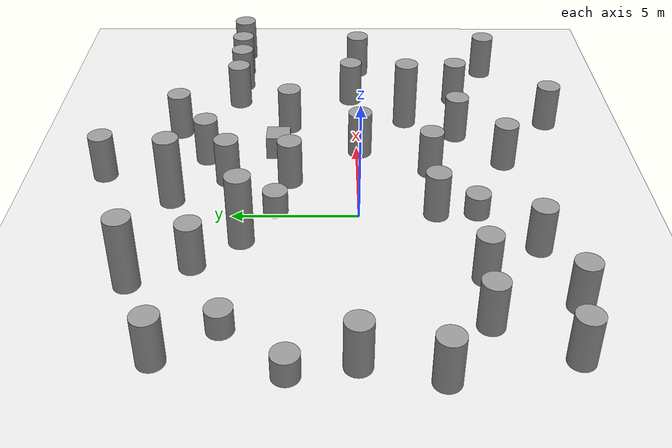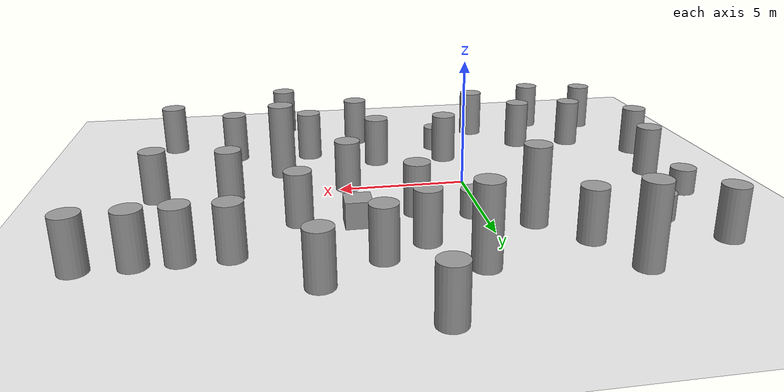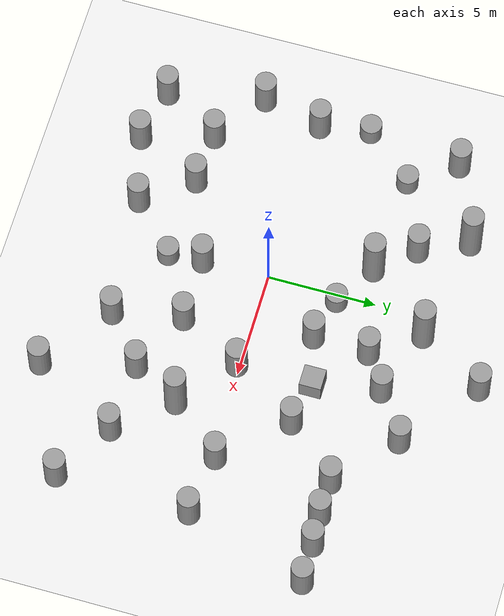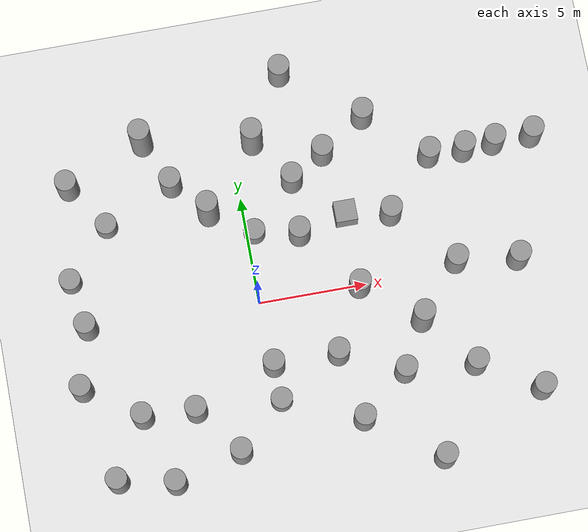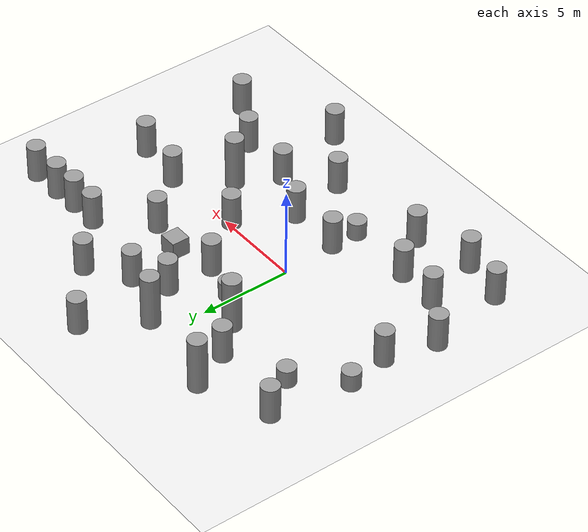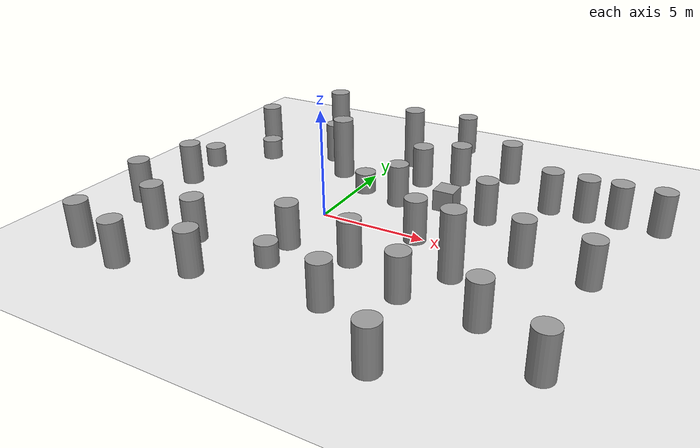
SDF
<sdf version="1.6">
 <world name="default">
  <scene><ambient>0.4 0.4 0.4 1</ambient><background>0.25 0.25 0.25 1</background><shadows>0</shadows></scene>
  <light name="sun" type="directional">
   <pose>0 0 10 0 -0 0</pose>
   <diffuse>0.7 0.7 0.7 0.5</diffuse>
   <specular>1 1 1 0.5</specular>
   <attenuation>
    <range>100</range>
    <constant>0.9</constant>
    <linear>0.01</linear>
    <quadratic>0.001</quadratic>
   </attenuation>
   <direction>0 0 -1</direction>
  </light>
  <model name="ground_plane">
   <static>1</static>
   <link name="link">
    <collision name="collision">
     <geometry><plane><normal>0 0 1</normal><size>100 100</size></plane></geometry>
     <surface><friction><ode><mu>100</mu><mu2>50</mu2></ode></friction></surface>
    </collision>
    <visual name="visual">
     <geometry><plane><normal>0 0 1</normal><size>100 100</size></plane></geometry>
     <material>
      <script><uri>file://media/materials/scripts/gazebo.material</uri><name>Gazebo/White</name></script>
     </material>
    </visual>
   </link>
  </model>
  <physics name="default_physics" default="0" type="ode">
   <ode>
    <solver>
     <type>quick</type>
     <iters>10</iters>
     <sor>1.3</sor>
     <use_dynamic_moi_rescaling>0</use_dynamic_moi_rescaling>
    </solver>
    <constraints>
     <cfm>0</cfm>
     <erp>0.2</erp>
     <contact_max_correcting_vel>100</contact_max_correcting_vel>
     <contact_surface_layer>0.001</contact_surface_layer>
    </constraints>
   </ode>
   <max_step_size>0.004</max_step_size>
   <real_time_factor>1</real_time_factor>
   <real_time_update_rate>250</real_time_update_rate>
  </physics>
  <gravity>0 0 -9.8066</gravity>
  <magnetic_field>6e-06 2.3e-05 -4.2e-05</magnetic_field>
  <atmosphere type="adiabatic"/>
  <scene><ambient>0.4 0.4 0.4 1</ambient><background>0.7 0.7 0.7 1</background><shadows>1</shadows></scene>
  <spherical_coordinates>
   <surface_model>EARTH_WGS84</surface_model>
   <latitude_deg>0</latitude_deg>
   <longitude_deg>0</longitude_deg>
   <elevation>0</elevation>
   <heading_deg>0</heading_deg>
  </spherical_coordinates>
  <model name="unit_cylinder_5">
   <link name="link">
    <inertial>
     <mass>1</mass>
     <inertia><ixx>0.145833</ixx><ixy>0</ixy><ixz>0</ixz><iyy>0.145833</iyy><iyz>0</iyz><izz>0.125</izz></inertia>
    </inertial>
    <visual name="visual">
     <geometry><cylinder><radius>0.5</radius><length>2</length></cylinder></geometry>
     <material>
      <script><name>Gazebo/Grey</name><uri>file://media/materials/scripts/gazebo.material</uri></script>
      <ambient>0.3 0.3 0.3 1</ambient>
      <diffuse>0.7 0.7 0.7 1</diffuse>
      <specular>0.01 0.01 0.01 1</specular>
      <emissive>0 0 0 1</emissive>
      <shader type="vertex"><normal_map>__default__</normal_map></shader>
     </material>
    </visual>
    <collision name="collision">
     <geometry><cylinder><radius>0.5</radius><length>2</length></cylinder></geometry>
     <surface>
      <friction>
       <ode><mu>1</mu><mu2>1</mu2><fdir1>0 0 0</fdir1><slip1>0</slip1><slip2>0</slip2></ode>
       <torsional>
        <coefficient>1</coefficient>
        <patch_radius>0</patch_radius>
        <surface_radius>0</surface_radius>
        <use_patch_radius>1</use_patch_radius>
        <ode><slip>0</slip></ode>
       </torsional>
      </friction>
      <bounce><restitution_coefficient>0</restitution_coefficient><threshold>1e+06</threshold></bounce>
      <contact>
       <collide_without_contact>0</collide_without_contact>
       <collide_without_contact_bitmask>1</collide_without_contact_bitmask>
       <collide_bitmask>1</collide_bitmask>
       <ode>
        <soft_cfm>0</soft_cfm>
        <soft_erp>0.2</soft_erp>
        <kp>1e+13</kp>
        <kd>1</kd>
        <max_vel>0.01</max_vel>
        <min_depth>0</min_depth>
       </ode>
       <bullet>
        <split_impulse>1</split_impulse>
        <split_impulse_penetration_threshold>-0.01</split_impulse_penetration_threshold>
        <soft_cfm>0</soft_cfm>
        <soft_erp>0.2</soft_erp>
        <kp>1e+13</kp>
        <kd>1</kd>
       </bullet>
      </contact>
     </surface>
    </collision>
   </link>
   <static>0</static>
   <pose>4.65515 -0.124311 0.999884 2.2e-05 -2e-06 0.004615</pose>
  </model>
  <model name="unit_cylinder_5_clone">
   <link name="link">
    <inertial>
     <mass>1</mass>
     <inertia><ixx>0.145833</ixx><ixy>0</ixy><ixz>0</ixz><iyy>0.145833</iyy><iyz>0</iyz><izz>0.125</izz></inertia>
    </inertial>
    <visual name="visual">
     <geometry><cylinder><radius>0.5</radius><length>2</length></cylinder></geometry>
     <material>
      <script><name>Gazebo/Grey</name><uri>file://media/materials/scripts/gazebo.material</uri></script>
      <ambient>0.3 0.3 0.3 1</ambient>
      <diffuse>0.7 0.7 0.7 1</diffuse>
      <specular>0.01 0.01 0.01 1</specular>
      <emissive>0 0 0 1</emissive>
      <shader type="vertex"><normal_map>__default__</normal_map></shader>
     </material>
    </visual>
    <collision name="collision">
     <geometry><cylinder><radius>0.5</radius><length>2</length></cylinder></geometry>
     <surface>
      <friction>
       <ode><mu>1</mu><mu2>1</mu2><fdir1>0 0 0</fdir1><slip1>0</slip1><slip2>0</slip2></ode>
       <torsional>
        <coefficient>1</coefficient>
        <patch_radius>0</patch_radius>
        <surface_radius>0</surface_radius>
        <use_patch_radius>1</use_patch_radius>
        <ode><slip>0</slip></ode>
       </torsional>
      </friction>
      <bounce><restitution_coefficient>0</restitution_coefficient><threshold>1e+06</threshold></bounce>
      <contact>
       <collide_without_contact>0</collide_without_contact>
       <collide_without_contact_bitmask>1</collide_without_contact_bitmask>
       <collide_bitmask>1</collide_bitmask>
       <ode>
        <soft_cfm>0</soft_cfm>
        <soft_erp>0.2</soft_erp>
        <kp>1e+13</kp>
        <kd>1</kd>
        <max_vel>0.01</max_vel>
        <min_depth>0</min_depth>
       </ode>
       <bullet>
        <split_impulse>1</split_impulse>
        <split_impulse_penetration_threshold>-0.01</split_impulse_penetration_threshold>
        <soft_cfm>0</soft_cfm>
        <soft_erp>0.2</soft_erp>
        <kp>1e+13</kp>
        <kd>1</kd>
       </bullet>
      </contact>
     </surface>
    </collision>
   </link>
   <static>0</static>
   <pose>2.38828 2.78335 0.999884 2.2e-05 -1e-06 0.002315</pose>
  </model>
  <model name="unit_cylinder_5_clone_0">
   <link name="link">
    <inertial>
     <mass>1</mass>
     <inertia><ixx>0.145833</ixx><ixy>0</ixy><ixz>0</ixz><iyy>0.145833</iyy><iyz>0</iyz><izz>0.125</izz></inertia>
    </inertial>
    <visual name="visual">
     <geometry><cylinder><radius>0.5</radius><length>2</length></cylinder></geometry>
     <material>
      <script><name>Gazebo/Grey</name><uri>file://media/materials/scripts/gazebo.material</uri></script>
      <ambient>0.3 0.3 0.3 1</ambient>
      <diffuse>0.7 0.7 0.7 1</diffuse>
      <specular>0.01 0.01 0.01 1</specular>
      <emissive>0 0 0 1</emissive>
      <shader type="vertex"><normal_map>__default__</normal_map></shader>
     </material>
    </visual>
    <collision name="collision">
     <geometry><cylinder><radius>0.5</radius><length>2</length></cylinder></geometry>
     <surface>
      <friction>
       <ode><mu>1</mu><mu2>1</mu2><fdir1>0 0 0</fdir1><slip1>0</slip1><slip2>0</slip2></ode>
       <torsional>
        <coefficient>1</coefficient>
        <patch_radius>0</patch_radius>
        <surface_radius>0</surface_radius>
        <use_patch_radius>1</use_patch_radius>
        <ode><slip>0</slip></ode>
       </torsional>
      </friction>
      <bounce><restitution_coefficient>0</restitution_coefficient><threshold>1e+06</threshold></bounce>
      <contact>
       <collide_without_contact>0</collide_without_contact>
       <collide_without_contact_bitmask>1</collide_without_contact_bitmask>
       <collide_bitmask>1</collide_bitmask>
       <ode>
        <soft_cfm>0</soft_cfm>
        <soft_erp>0.2</soft_erp>
        <kp>1e+13</kp>
        <kd>1</kd>
        <max_vel>0.01</max_vel>
        <min_depth>0</min_depth>
       </ode>
       <bullet>
        <split_impulse>1</split_impulse>
        <split_impulse_penetration_threshold>-0.01</split_impulse_penetration_threshold>
        <soft_cfm>0</soft_cfm>
        <soft_erp>0.2</soft_erp>
        <kp>1e+13</kp>
        <kd>1</kd>
       </bullet>
      </contact>
     </surface>
    </collision>
   </link>
   <static>0</static>
   <pose>0.149287 -3.03613 0.999884 2.2e-05 -1e-06 0.002298</pose>
  </model>
  <model name="unit_cylinder_5_clone_3">
   <link name="link">
    <inertial>
     <mass>1</mass>
     <inertia><ixx>0.145833</ixx><ixy>0</ixy><ixz>0</ixz><iyy>0.145833</iyy><iyz>0</iyz><izz>0.125</izz></inertia>
    </inertial>
    <visual name="visual">
     <geometry><cylinder><radius>0.5</radius><length>2</length></cylinder></geometry>
     <material>
      <script><name>Gazebo/Grey</name><uri>file://media/materials/scripts/gazebo.material</uri></script>
      <ambient>0.3 0.3 0.3 1</ambient>
      <diffuse>0.7 0.7 0.7 1</diffuse>
      <specular>0.01 0.01 0.01 1</specular>
      <emissive>0 0 0 1</emissive>
      <shader type="vertex"><normal_map>__default__</normal_map></shader>
     </material>
    </visual>
    <collision name="collision">
     <geometry><cylinder><radius>0.5</radius><length>2</length></cylinder></geometry>
     <surface>
      <friction>
       <ode><mu>1</mu><mu2>1</mu2><fdir1>0 0 0</fdir1><slip1>0</slip1><slip2>0</slip2></ode>
       <torsional>
        <coefficient>1</coefficient>
        <patch_radius>0</patch_radius>
        <surface_radius>0</surface_radius>
        <use_patch_radius>1</use_patch_radius>
        <ode><slip>0</slip></ode>
       </torsional>
      </friction>
      <bounce><restitution_coefficient>0</restitution_coefficient><threshold>1e+06</threshold></bounce>
      <contact>
       <collide_without_contact>0</collide_without_contact>
       <collide_without_contact_bitmask>1</collide_without_contact_bitmask>
       <collide_bitmask>1</collide_bitmask>
       <ode>
        <soft_cfm>0</soft_cfm>
        <soft_erp>0.2</soft_erp>
        <kp>1e+13</kp>
        <kd>1</kd>
        <max_vel>0.01</max_vel>
        <min_depth>0</min_depth>
       </ode>
       <bullet>
        <split_impulse>1</split_impulse>
        <split_impulse_penetration_threshold>-0.01</split_impulse_penetration_threshold>
        <soft_cfm>0</soft_cfm>
        <soft_erp>0.2</soft_erp>
        <kp>1e+13</kp>
        <kd>1</kd>
       </bullet>
      </contact>
     </surface>
    </collision>
   </link>
   <static>0</static>
   <pose>-3.66733 -4.47285 0.999884 2.2e-05 -1e-06 0.000409</pose>
  </model>
  <model name="unit_cylinder_5_clone_4">
   <link name="link">
    <inertial>
     <mass>1</mass>
     <inertia><ixx>0.145833</ixx><ixy>0</ixy><ixz>0</ixz><iyy>0.145833</iyy><iyz>0</iyz><izz>0.125</izz></inertia>
    </inertial>
    <visual name="visual">
     <geometry><cylinder><radius>0.5</radius><length>2</length></cylinder></geometry>
     <material>
      <script><name>Gazebo/Grey</name><uri>file://media/materials/scripts/gazebo.material</uri></script>
      <ambient>0.3 0.3 0.3 1</ambient>
      <diffuse>0.7 0.7 0.7 1</diffuse>
      <specular>0.01 0.01 0.01 1</specular>
      <emissive>0 0 0 1</emissive>
      <shader type="vertex"><normal_map>__default__</normal_map></shader>
     </material>
    </visual>
    <collision name="collision">
     <geometry><cylinder><radius>0.5</radius><length>2</length></cylinder></geometry>
     <surface>
      <friction>
       <ode><mu>1</mu><mu2>1</mu2><fdir1>0 0 0</fdir1><slip1>0</slip1><slip2>0</slip2></ode>
       <torsional>
        <coefficient>1</coefficient>
        <patch_radius>0</patch_radius>
        <surface_radius>0</surface_radius>
        <use_patch_radius>1</use_patch_radius>
        <ode><slip>0</slip></ode>
       </torsional>
      </friction>
      <bounce><restitution_coefficient>0</restitution_coefficient><threshold>1e+06</threshold></bounce>
      <contact>
       <collide_without_contact>0</collide_without_contact>
       <collide_without_contact_bitmask>1</collide_without_contact_bitmask>
       <collide_bitmask>1</collide_bitmask>
       <ode>
        <soft_cfm>0</soft_cfm>
        <soft_erp>0.2</soft_erp>
        <kp>1e+13</kp>
        <kd>1</kd>
        <max_vel>0.01</max_vel>
        <min_depth>0</min_depth>
       </ode>
       <bullet>
        <split_impulse>1</split_impulse>
        <split_impulse_penetration_threshold>-0.01</split_impulse_penetration_threshold>
        <soft_cfm>0</soft_cfm>
        <soft_erp>0.2</soft_erp>
        <kp>1e+13</kp>
        <kd>1</kd>
       </bullet>
      </contact>
     </surface>
    </collision>
   </link>
   <static>0</static>
   <pose>-7.93374 0.169664 0.999884 2.2e-05 -1e-06 -0.003062</pose>
  </model>
  <model name="unit_cylinder_5_clone_5">
   <link name="link">
    <inertial>
     <mass>1</mass>
     <inertia><ixx>0.145833</ixx><ixy>0</ixy><ixz>0</ixz><iyy>0.145833</iyy><iyz>0</iyz><izz>0.125</izz></inertia>
    </inertial>
    <visual name="visual">
     <geometry><cylinder><radius>0.5</radius><length>2</length></cylinder></geometry>
     <material>
      <script><name>Gazebo/Grey</name><uri>file://media/materials/scripts/gazebo.material</uri></script>
      <ambient>0.3 0.3 0.3 1</ambient>
      <diffuse>0.7 0.7 0.7 1</diffuse>
      <specular>0.01 0.01 0.01 1</specular>
      <emissive>0 0 0 1</emissive>
      <shader type="vertex"><normal_map>__default__</normal_map></shader>
     </material>
    </visual>
    <collision name="collision">
     <geometry><cylinder><radius>0.5</radius><length>2</length></cylinder></geometry>
     <surface>
      <friction>
       <ode><mu>1</mu><mu2>1</mu2><fdir1>0 0 0</fdir1><slip1>0</slip1><slip2>0</slip2></ode>
       <torsional>
        <coefficient>1</coefficient>
        <patch_radius>0</patch_radius>
        <surface_radius>0</surface_radius>
        <use_patch_radius>1</use_patch_radius>
        <ode><slip>0</slip></ode>
       </torsional>
      </friction>
      <bounce><restitution_coefficient>0</restitution_coefficient><threshold>1e+06</threshold></bounce>
      <contact>
       <collide_without_contact>0</collide_without_contact>
       <collide_without_contact_bitmask>1</collide_without_contact_bitmask>
       <collide_bitmask>1</collide_bitmask>
       <ode>
        <soft_cfm>0</soft_cfm>
        <soft_erp>0.2</soft_erp>
        <kp>1e+13</kp>
        <kd>1</kd>
        <max_vel>0.01</max_vel>
        <min_depth>0</min_depth>
       </ode>
       <bullet>
        <split_impulse>1</split_impulse>
        <split_impulse_penetration_threshold>-0.01</split_impulse_penetration_threshold>
        <soft_cfm>0</soft_cfm>
        <soft_erp>0.2</soft_erp>
        <kp>1e+13</kp>
        <kd>1</kd>
       </bullet>
      </contact>
     </surface>
    </collision>
   </link>
   <static>0</static>
   <pose>-8.58869 -2.60629 0.999884 2.2e-05 -1e-06 -0.00547</pose>
  </model>
  <model name="unit_cylinder_5_clone_6">
   <link name="link">
    <inertial>
     <mass>1</mass>
     <inertia><ixx>0.145833</ixx><ixy>0</ixy><ixz>0</ixz><iyy>0.145833</iyy><iyz>0</iyz><izz>0.125</izz></inertia>
    </inertial>
    <visual name="visual">
     <geometry><cylinder><radius>0.5</radius><length>2</length></cylinder></geometry>
     <material>
      <script><name>Gazebo/Grey</name><uri>file://media/materials/scripts/gazebo.material</uri></script>
      <ambient>0.3 0.3 0.3 1</ambient>
      <diffuse>0.7 0.7 0.7 1</diffuse>
      <specular>0.01 0.01 0.01 1</specular>
      <emissive>0 0 0 1</emissive>
      <shader type="vertex"><normal_map>__default__</normal_map></shader>
     </material>
    </visual>
    <collision name="collision">
     <geometry><cylinder><radius>0.5</radius><length>2</length></cylinder></geometry>
     <surface>
      <friction>
       <ode><mu>1</mu><mu2>1</mu2><fdir1>0 0 0</fdir1><slip1>0</slip1><slip2>0</slip2></ode>
       <torsional>
        <coefficient>1</coefficient>
        <patch_radius>0</patch_radius>
        <surface_radius>0</surface_radius>
        <use_patch_radius>1</use_patch_radius>
        <ode><slip>0</slip></ode>
       </torsional>
      </friction>
      <bounce><restitution_coefficient>0</restitution_coefficient><threshold>1e+06</threshold></bounce>
      <contact>
       <collide_without_contact>0</collide_without_contact>
       <collide_without_contact_bitmask>1</collide_without_contact_bitmask>
       <collide_bitmask>1</collide_bitmask>
       <ode>
        <soft_cfm>0</soft_cfm>
        <soft_erp>0.2</soft_erp>
        <kp>1e+13</kp>
        <kd>1</kd>
        <max_vel>0.01</max_vel>
        <min_depth>0</min_depth>
       </ode>
       <bullet>
        <split_impulse>1</split_impulse>
        <split_impulse_penetration_threshold>-0.01</split_impulse_penetration_threshold>
        <soft_cfm>0</soft_cfm>
        <soft_erp>0.2</soft_erp>
        <kp>1e+13</kp>
        <kd>1</kd>
       </bullet>
      </contact>
     </surface>
    </collision>
   </link>
   <static>0</static>
   <pose>6.68619 2.97584 0.999884 2.2e-05 -1e-06 1.9e-05</pose>
  </model>
  <model name="unit_cylinder_5_clone_7">
   <link name="link">
    <inertial>
     <mass>1</mass>
     <inertia><ixx>0.145833</ixx><ixy>0</ixy><ixz>0</ixz><iyy>0.145833</iyy><iyz>0</iyz><izz>0.125</izz></inertia>
    </inertial>
    <visual name="visual">
     <geometry><cylinder><radius>0.5</radius><length>2</length></cylinder></geometry>
     <material>
      <script><name>Gazebo/Grey</name><uri>file://media/materials/scripts/gazebo.material</uri></script>
      <ambient>0.3 0.3 0.3 1</ambient>
      <diffuse>0.7 0.7 0.7 1</diffuse>
      <specular>0.01 0.01 0.01 1</specular>
      <emissive>0 0 0 1</emissive>
      <shader type="vertex"><normal_map>__default__</normal_map></shader>
     </material>
    </visual>
    <collision name="collision">
     <geometry><cylinder><radius>0.5</radius><length>2</length></cylinder></geometry>
     <surface>
      <friction>
       <ode><mu>1</mu><mu2>1</mu2><fdir1>0 0 0</fdir1><slip1>0</slip1><slip2>0</slip2></ode>
       <torsional>
        <coefficient>1</coefficient>
        <patch_radius>0</patch_radius>
        <surface_radius>0</surface_radius>
        <use_patch_radius>1</use_patch_radius>
        <ode><slip>0</slip></ode>
       </torsional>
      </friction>
      <bounce><restitution_coefficient>0</restitution_coefficient><threshold>1e+06</threshold></bounce>
      <contact>
       <collide_without_contact>0</collide_without_contact>
       <collide_without_contact_bitmask>1</collide_without_contact_bitmask>
       <collide_bitmask>1</collide_bitmask>
       <ode>
        <soft_cfm>0</soft_cfm>
        <soft_erp>0.2</soft_erp>
        <kp>1e+13</kp>
        <kd>1</kd>
        <max_vel>0.01</max_vel>
        <min_depth>0</min_depth>
       </ode>
       <bullet>
        <split_impulse>1</split_impulse>
        <split_impulse_penetration_threshold>-0.01</split_impulse_penetration_threshold>
        <soft_cfm>0</soft_cfm>
        <soft_erp>0.2</soft_erp>
        <kp>1e+13</kp>
        <kd>1</kd>
       </bullet>
      </contact>
     </surface>
    </collision>
   </link>
   <static>0</static>
   <pose>5.97232 -4.3731 0.999884 2.2e-05 -1e-06 0.002884</pose>
  </model>
  <model name="unit_cylinder_0">
   <pose>0.360811 3.27692 0.499884 3e-06 -3e-06 -0.000418</pose>
   <link name="link">
    <inertial>
     <mass>1</mass>
     <inertia><ixx>0.145833</ixx><ixy>0</ixy><ixz>0</ixz><iyy>0.145833</iyy><iyz>0</iyz><izz>0.125</izz></inertia>
    </inertial>
    <collision name="collision">
     <geometry><cylinder><radius>0.5</radius><length>1</length></cylinder></geometry>
    </collision>
    <visual name="visual">
     <geometry><cylinder><radius>0.5</radius><length>1</length></cylinder></geometry>
     <material>
      <script><name>Gazebo/Grey</name><uri>file://media/materials/scripts/gazebo.material</uri></script>
     </material>
    </visual>
   </link>
  </model>
  <model name="unit_box_0">
   <pose>4.62964 3.37332 0.499944 2e-06 0.000108 -0.001429</pose>
   <link name="link">
    <inertial>
     <mass>1</mass>
     <inertia>
      <ixx>0.166667</ixx>
      <ixy>0</ixy>
      <ixz>0</ixz>
      <iyy>0.166667</iyy>
      <iyz>0</iyz>
      <izz>0.166667</izz>
     </inertia>
    </inertial>
    <collision name="collision"><geometry><box><size>1 1 1</size></box></geometry></collision>
    <visual name="visual">
     <geometry><box><size>1 1 1</size></box></geometry>
     <material>
      <script><name>Gazebo/Grey</name><uri>file://media/materials/scripts/gazebo.material</uri></script>
     </material>
    </visual>
   </link>
  </model>
  <model name="unit_cylinder_1">
   <pose>0.210065 -4.63987 0.499884 3e-06 -3e-06 -0.000165</pose>
   <link name="link">
    <inertial>
     <mass>1</mass>
     <inertia><ixx>0.145833</ixx><ixy>0</ixy><ixz>0</ixz><iyy>0.145833</iyy><iyz>0</iyz><izz>0.125</izz></inertia>
    </inertial>
    <collision name="collision">
     <geometry><cylinder><radius>0.5</radius><length>1</length></cylinder></geometry>
    </collision>
    <visual name="visual">
     <geometry><cylinder><radius>0.5</radius><length>1</length></cylinder></geometry>
     <material>
      <script><name>Gazebo/Grey</name><uri>file://media/materials/scripts/gazebo.material</uri></script>
     </material>
    </visual>
   </link>
  </model>
  <model name="unit_cylinder_1_clone_0">
   <pose>-6.29638 4.76436 0.499972 -5.4e-05 5.5e-05 -0.000122</pose>
   <link name="link">
    <inertial>
     <mass>1</mass>
     <inertia><ixx>0.145833</ixx><ixy>0</ixy><ixz>0</ixz><iyy>0.145833</iyy><iyz>0</iyz><izz>0.125</izz></inertia>
    </inertial>
    <collision name="collision">
     <geometry><cylinder><radius>0.5</radius><length>1</length></cylinder></geometry>
    </collision>
    <visual name="visual">
     <geometry><cylinder><radius>0.5</radius><length>1</length></cylinder></geometry>
     <material>
      <script><name>Gazebo/Grey</name><uri>file://media/materials/scripts/gazebo.material</uri></script>
     </material>
    </visual>
   </link>
  </model>
  <model name="unit_cylinder_1_clone_1">
   <pose>-8.33577 2.47754 0.499972 -5.4e-05 5.5e-05 0.001407</pose>
   <link name="link">
    <inertial>
     <mass>1</mass>
     <inertia><ixx>0.145833</ixx><ixy>0</ixy><ixz>0</ixz><iyy>0.145833</iyy><iyz>0</iyz><izz>0.125</izz></inertia>
    </inertial>
    <collision name="collision">
     <geometry><cylinder><radius>0.5</radius><length>1</length></cylinder></geometry>
    </collision>
    <visual name="visual">
     <geometry><cylinder><radius>0.5</radius><length>1</length></cylinder></geometry>
     <material>
      <script><name>Gazebo/Grey</name><uri>file://media/materials/scripts/gazebo.material</uri></script>
     </material>
    </visual>
   </link>
  </model>
  <model name="unit_cylinder_0_0">
   <link name="link">
    <inertial>
     <mass>1</mass>
     <inertia><ixx>0.145833</ixx><ixy>0</ixy><ixz>0</ixz><iyy>0.145833</iyy><iyz>0</iyz><izz>0.125</izz></inertia>
    </inertial>
    <visual name="visual">
     <geometry><cylinder><radius>0.5</radius><length>3</length></cylinder></geometry>
     <material>
      <script><name>Gazebo/Grey</name><uri>file://media/materials/scripts/gazebo.material</uri></script>
      <ambient>0.3 0.3 0.3 1</ambient>
      <diffuse>0.7 0.7 0.7 1</diffuse>
      <specular>0.01 0.01 0.01 1</specular>
      <emissive>0 0 0 1</emissive>
      <shader type="vertex"><normal_map>__default__</normal_map></shader>
     </material>
    </visual>
    <collision name="collision">
     <geometry><cylinder><radius>0.5</radius><length>3</length></cylinder></geometry>
     <surface>
      <friction>
       <ode><mu>1</mu><mu2>1</mu2><fdir1>0 0 0</fdir1><slip1>0</slip1><slip2>0</slip2></ode>
       <torsional>
        <coefficient>1</coefficient>
        <patch_radius>0</patch_radius>
        <surface_radius>0</surface_radius>
        <use_patch_radius>1</use_patch_radius>
        <ode><slip>0</slip></ode>
       </torsional>
      </friction>
      <bounce><restitution_coefficient>0</restitution_coefficient><threshold>1e+06</threshold></bounce>
      <contact>
       <collide_without_contact>0</collide_without_contact>
       <collide_without_contact_bitmask>1</collide_without_contact_bitmask>
       <collide_bitmask>1</collide_bitmask>
       <ode>
        <soft_cfm>0</soft_cfm>
        <soft_erp>0.2</soft_erp>
        <kp>1e+13</kp>
        <kd>1</kd>
        <max_vel>0.01</max_vel>
        <min_depth>0</min_depth>
       </ode>
       <bullet>
        <split_impulse>1</split_impulse>
        <split_impulse_penetration_threshold>-0.01</split_impulse_penetration_threshold>
        <soft_cfm>0</soft_cfm>
        <soft_erp>0.2</soft_erp>
        <kp>1e+13</kp>
        <kd>1</kd>
       </bullet>
      </contact>
     </surface>
    </collision>
   </link>
   <static>0</static>
   <pose>7.16627 -2.19502 1.49988 4.7e-05 -4e-06 -0.002805</pose>
  </model>
  <model name="unit_cylinder_5_clone_1_clone">
   <link name="link">
    <inertial>
     <mass>1</mass>
     <inertia><ixx>0.145833</ixx><ixy>0</ixy><ixz>0</ixz><iyy>0.145833</iyy><iyz>0</iyz><izz>0.125</izz></inertia>
    </inertial>
    <visual name="visual">
     <geometry><cylinder><radius>0.5</radius><length>2</length></cylinder></geometry>
     <material>
      <script><name>Gazebo/Grey</name><uri>file://media/materials/scripts/gazebo.material</uri></script>
      <ambient>0.3 0.3 0.3 1</ambient>
      <diffuse>0.7 0.7 0.7 1</diffuse>
      <specular>0.01 0.01 0.01 1</specular>
      <emissive>0 0 0 1</emissive>
      <shader type="vertex"><normal_map>__default__</normal_map></shader>
     </material>
    </visual>
    <collision name="collision">
     <geometry><cylinder><radius>0.5</radius><length>2</length></cylinder></geometry>
     <surface>
      <friction>
       <ode><mu>1</mu><mu2>1</mu2><fdir1>0 0 0</fdir1><slip1>0</slip1><slip2>0</slip2></ode>
       <torsional>
        <coefficient>1</coefficient>
        <patch_radius>0</patch_radius>
        <surface_radius>0</surface_radius>
        <use_patch_radius>1</use_patch_radius>
        <ode><slip>0</slip></ode>
       </torsional>
      </friction>
      <bounce><restitution_coefficient>0</restitution_coefficient><threshold>1e+06</threshold></bounce>
      <contact>
       <collide_without_contact>0</collide_without_contact>
       <collide_without_contact_bitmask>1</collide_without_contact_bitmask>
       <collide_bitmask>1</collide_bitmask>
       <ode>
        <soft_cfm>0</soft_cfm>
        <soft_erp>0.2</soft_erp>
        <kp>1e+13</kp>
        <kd>1</kd>
        <max_vel>0.01</max_vel>
        <min_depth>0</min_depth>
       </ode>
       <bullet>
        <split_impulse>1</split_impulse>
        <split_impulse_penetration_threshold>-0.01</split_impulse_penetration_threshold>
        <soft_cfm>0</soft_cfm>
        <soft_erp>0.2</soft_erp>
        <kp>1e+13</kp>
        <kd>1</kd>
       </bullet>
      </contact>
     </surface>
    </collision>
   </link>
   <static>0</static>
   <pose>2.48657 5.3464 0.999884 2.2e-05 -1e-06 -0.002392</pose>
  </model>
  <model name="unit_cylinder_5_clone_1_clone_0">
   <link name="link">
    <inertial>
     <mass>1</mass>
     <inertia><ixx>0.145833</ixx><ixy>0</ixy><ixz>0</ixz><iyy>0.145833</iyy><iyz>0</iyz><izz>0.125</izz></inertia>
    </inertial>
    <visual name="visual">
     <geometry><cylinder><radius>0.5</radius><length>2</length></cylinder></geometry>
     <material>
      <script><name>Gazebo/Grey</name><uri>file://media/materials/scripts/gazebo.material</uri></script>
      <ambient>0.3 0.3 0.3 1</ambient>
      <diffuse>0.7 0.7 0.7 1</diffuse>
      <specular>0.01 0.01 0.01 1</specular>
      <emissive>0 0 0 1</emissive>
      <shader type="vertex"><normal_map>__default__</normal_map></shader>
     </material>
    </visual>
    <collision name="collision">
     <geometry><cylinder><radius>0.5</radius><length>2</length></cylinder></geometry>
     <surface>
      <friction>
       <ode><mu>1</mu><mu2>1</mu2><fdir1>0 0 0</fdir1><slip1>0</slip1><slip2>0</slip2></ode>
       <torsional>
        <coefficient>1</coefficient>
        <patch_radius>0</patch_radius>
        <surface_radius>0</surface_radius>
        <use_patch_radius>1</use_patch_radius>
        <ode><slip>0</slip></ode>
       </torsional>
      </friction>
      <bounce><restitution_coefficient>0</restitution_coefficient><threshold>1e+06</threshold></bounce>
      <contact>
       <collide_without_contact>0</collide_without_contact>
       <collide_without_contact_bitmask>1</collide_without_contact_bitmask>
       <collide_bitmask>1</collide_bitmask>
       <ode>
        <soft_cfm>0</soft_cfm>
        <soft_erp>0.2</soft_erp>
        <kp>1e+13</kp>
        <kd>1</kd>
        <max_vel>0.01</max_vel>
        <min_depth>0</min_depth>
       </ode>
       <bullet>
        <split_impulse>1</split_impulse>
        <split_impulse_penetration_threshold>-0.01</split_impulse_penetration_threshold>
        <soft_cfm>0</soft_cfm>
        <soft_erp>0.2</soft_erp>
        <kp>1e+13</kp>
        <kd>1</kd>
       </bullet>
      </contact>
     </surface>
    </collision>
   </link>
   <static>0</static>
   <pose>-3.04049 6.13018 0.999884 2.2e-05 -1e-06 -0.001363</pose>
  </model>
  <model name="unit_cylinder_0_0_clone_clone">
   <link name="link">
    <inertial>
     <mass>1</mass>
     <inertia><ixx>0.145833</ixx><ixy>0</ixy><ixz>0</ixz><iyy>0.145833</iyy><iyz>0</iyz><izz>0.125</izz></inertia>
    </inertial>
    <visual name="visual">
     <geometry><cylinder><radius>0.5</radius><length>3</length></cylinder></geometry>
     <material>
      <script><name>Gazebo/Grey</name><uri>file://media/materials/scripts/gazebo.material</uri></script>
      <ambient>0.3 0.3 0.3 1</ambient>
      <diffuse>0.7 0.7 0.7 1</diffuse>
      <specular>0.01 0.01 0.01 1</specular>
      <emissive>0 0 0 1</emissive>
      <shader type="vertex"><normal_map>__default__</normal_map></shader>
     </material>
    </visual>
    <collision name="collision">
     <geometry><cylinder><radius>0.5</radius><length>3</length></cylinder></geometry>
     <surface>
      <friction>
       <ode><mu>1</mu><mu2>1</mu2><fdir1>0 0 0</fdir1><slip1>0</slip1><slip2>0</slip2></ode>
       <torsional>
        <coefficient>1</coefficient>
        <patch_radius>0</patch_radius>
        <surface_radius>0</surface_radius>
        <use_patch_radius>1</use_patch_radius>
        <ode><slip>0</slip></ode>
       </torsional>
      </friction>
      <bounce><restitution_coefficient>0</restitution_coefficient><threshold>1e+06</threshold></bounce>
      <contact>
       <collide_without_contact>0</collide_without_contact>
       <collide_without_contact_bitmask>1</collide_without_contact_bitmask>
       <collide_bitmask>1</collide_bitmask>
       <ode>
        <soft_cfm>0</soft_cfm>
        <soft_erp>0.2</soft_erp>
        <kp>1e+13</kp>
        <kd>1</kd>
        <max_vel>0.01</max_vel>
        <min_depth>0</min_depth>
       </ode>
       <bullet>
        <split_impulse>1</split_impulse>
        <split_impulse_penetration_threshold>-0.01</split_impulse_penetration_threshold>
        <soft_cfm>0</soft_cfm>
        <soft_erp>0.2</soft_erp>
        <kp>1e+13</kp>
        <kd>1</kd>
       </bullet>
      </contact>
     </surface>
    </collision>
   </link>
   <static>0</static>
   <pose>1.00231 7.45946 1.49988 4.7e-05 -4e-06 -0.006467</pose>
  </model>
  <model name="unit_cylinder_0_0_clone_clone_0">
   <link name="link">
    <inertial>
     <mass>1</mass>
     <inertia><ixx>0.145833</ixx><ixy>0</ixy><ixz>0</ixz><iyy>0.145833</iyy><iyz>0</iyz><izz>0.125</izz></inertia>
    </inertial>
    <visual name="visual">
     <geometry><cylinder><radius>0.5</radius><length>3</length></cylinder></geometry>
     <material>
      <script><name>Gazebo/Grey</name><uri>file://media/materials/scripts/gazebo.material</uri></script>
      <ambient>0.3 0.3 0.3 1</ambient>
      <diffuse>0.7 0.7 0.7 1</diffuse>
      <specular>0.01 0.01 0.01 1</specular>
      <emissive>0 0 0 1</emissive>
      <shader type="vertex"><normal_map>__default__</normal_map></shader>
     </material>
    </visual>
    <collision name="collision">
     <geometry><cylinder><radius>0.5</radius><length>3</length></cylinder></geometry>
     <surface>
      <friction>
       <ode><mu>1</mu><mu2>1</mu2><fdir1>0 0 0</fdir1><slip1>0</slip1><slip2>0</slip2></ode>
       <torsional>
        <coefficient>1</coefficient>
        <patch_radius>0</patch_radius>
        <surface_radius>0</surface_radius>
        <use_patch_radius>1</use_patch_radius>
        <ode><slip>0</slip></ode>
       </torsional>
      </friction>
      <bounce><restitution_coefficient>0</restitution_coefficient><threshold>1e+06</threshold></bounce>
      <contact>
       <collide_without_contact>0</collide_without_contact>
       <collide_without_contact_bitmask>1</collide_without_contact_bitmask>
       <collide_bitmask>1</collide_bitmask>
       <ode>
        <soft_cfm>0</soft_cfm>
        <soft_erp>0.2</soft_erp>
        <kp>1e+13</kp>
        <kd>1</kd>
        <max_vel>0.01</max_vel>
        <min_depth>0</min_depth>
       </ode>
       <bullet>
        <split_impulse>1</split_impulse>
        <split_impulse_penetration_threshold>-0.01</split_impulse_penetration_threshold>
        <soft_cfm>0</soft_cfm>
        <soft_erp>0.2</soft_erp>
        <kp>1e+13</kp>
        <kd>1</kd>
       </bullet>
      </contact>
     </surface>
    </collision>
   </link>
   <static>0</static>
   <pose>-4.03855 8.32066 1.49988 4.7e-05 -4e-06 -0.002883</pose>
  </model>
  <model name="unit_cylinder_0_0_clone_clone_1">
   <link name="link">
    <inertial>
     <mass>1</mass>
     <inertia><ixx>0.145833</ixx><ixy>0</ixy><ixz>0</ixz><iyy>0.145833</iyy><iyz>0</iyz><izz>0.125</izz></inertia>
    </inertial>
    <visual name="visual">
     <geometry><cylinder><radius>0.5</radius><length>3</length></cylinder></geometry>
     <material>
      <script><name>Gazebo/Grey</name><uri>file://media/materials/scripts/gazebo.material</uri></script>
      <ambient>0.3 0.3 0.3 1</ambient>
      <diffuse>0.7 0.7 0.7 1</diffuse>
      <specular>0.01 0.01 0.01 1</specular>
      <emissive>0 0 0 1</emissive>
      <shader type="vertex"><normal_map>__default__</normal_map></shader>
     </material>
    </visual>
    <collision name="collision">
     <geometry><cylinder><radius>0.5</radius><length>3</length></cylinder></geometry>
     <surface>
      <friction>
       <ode><mu>1</mu><mu2>1</mu2><fdir1>0 0 0</fdir1><slip1>0</slip1><slip2>0</slip2></ode>
       <torsional>
        <coefficient>1</coefficient>
        <patch_radius>0</patch_radius>
        <surface_radius>0</surface_radius>
        <use_patch_radius>1</use_patch_radius>
        <ode><slip>0</slip></ode>
       </torsional>
      </friction>
      <bounce><restitution_coefficient>0</restitution_coefficient><threshold>1e+06</threshold></bounce>
      <contact>
       <collide_without_contact>0</collide_without_contact>
       <collide_without_contact_bitmask>1</collide_without_contact_bitmask>
       <collide_bitmask>1</collide_bitmask>
       <ode>
        <soft_cfm>0</soft_cfm>
        <soft_erp>0.2</soft_erp>
        <kp>1e+13</kp>
        <kd>1</kd>
        <max_vel>0.01</max_vel>
        <min_depth>0</min_depth>
       </ode>
       <bullet>
        <split_impulse>1</split_impulse>
        <split_impulse_penetration_threshold>-0.01</split_impulse_penetration_threshold>
        <soft_cfm>0</soft_cfm>
        <soft_erp>0.2</soft_erp>
        <kp>1e+13</kp>
        <kd>1</kd>
       </bullet>
      </contact>
     </surface>
    </collision>
   </link>
   <static>0</static>
   <pose>-1.56798 4.46718 1.49988 4.7e-05 4e-06 0.003118</pose>
  </model>
  <model name="unit_cylinder_5_clone_0_clone">
   <link name="link">
    <inertial>
     <mass>1</mass>
     <inertia><ixx>0.145833</ixx><ixy>0</ixy><ixz>0</ixz><iyy>0.145833</iyy><iyz>0</iyz><izz>0.125</izz></inertia>
    </inertial>
    <visual name="visual">
     <geometry><cylinder><radius>0.5</radius><length>2</length></cylinder></geometry>
     <material>
      <script><name>Gazebo/Grey</name><uri>file://media/materials/scripts/gazebo.material</uri></script>
      <ambient>0.3 0.3 0.3 1</ambient>
      <diffuse>0.7 0.7 0.7 1</diffuse>
      <specular>0.01 0.01 0.01 1</specular>
      <emissive>0 0 0 1</emissive>
      <shader type="vertex"><normal_map>__default__</normal_map></shader>
     </material>
    </visual>
    <collision name="collision">
     <geometry><cylinder><radius>0.5</radius><length>2</length></cylinder></geometry>
     <surface>
      <friction>
       <ode><mu>1</mu><mu2>1</mu2><fdir1>0 0 0</fdir1><slip1>0</slip1><slip2>0</slip2></ode>
       <torsional>
        <coefficient>1</coefficient>
        <patch_radius>0</patch_radius>
        <surface_radius>0</surface_radius>
        <use_patch_radius>1</use_patch_radius>
        <ode><slip>0</slip></ode>
       </torsional>
      </friction>
      <bounce><restitution_coefficient>0</restitution_coefficient><threshold>1e+06</threshold></bounce>
      <contact>
       <collide_without_contact>0</collide_without_contact>
       <collide_without_contact_bitmask>1</collide_without_contact_bitmask>
       <collide_bitmask>1</collide_bitmask>
       <ode>
        <soft_cfm>0</soft_cfm>
        <soft_erp>0.2</soft_erp>
        <kp>1e+13</kp>
        <kd>1</kd>
        <max_vel>0.01</max_vel>
        <min_depth>0</min_depth>
       </ode>
       <bullet>
        <split_impulse>1</split_impulse>
        <split_impulse_penetration_threshold>-0.01</split_impulse_penetration_threshold>
        <soft_cfm>0</soft_cfm>
        <soft_erp>0.2</soft_erp>
        <kp>1e+13</kp>
        <kd>1</kd>
       </bullet>
      </contact>
     </surface>
    </collision>
   </link>
   <static>0</static>
   <pose>3.1338 -3.03548 0.999884 2.2e-05 -2e-06 0.003543</pose>
  </model>
  <model name="unit_cylinder_5_clone_0_clone_1">
   <link name="link">
    <inertial>
     <mass>1</mass>
     <inertia><ixx>0.145833</ixx><ixy>0</ixy><ixz>0</ixz><iyy>0.145833</iyy><iyz>0</iyz><izz>0.125</izz></inertia>
    </inertial>
    <visual name="visual">
     <geometry><cylinder><radius>0.5</radius><length>2</length></cylinder></geometry>
     <material>
      <script><name>Gazebo/Grey</name><uri>file://media/materials/scripts/gazebo.material</uri></script>
      <ambient>0.3 0.3 0.3 1</ambient>
      <diffuse>0.7 0.7 0.7 1</diffuse>
      <specular>0.01 0.01 0.01 1</specular>
      <emissive>0 0 0 1</emissive>
      <shader type="vertex"><normal_map>__default__</normal_map></shader>
     </material>
    </visual>
    <collision name="collision">
     <geometry><cylinder><radius>0.5</radius><length>2</length></cylinder></geometry>
     <surface>
      <friction>
       <ode><mu>1</mu><mu2>1</mu2><fdir1>0 0 0</fdir1><slip1>0</slip1><slip2>0</slip2></ode>
       <torsional>
        <coefficient>1</coefficient>
        <patch_radius>0</patch_radius>
        <surface_radius>0</surface_radius>
        <use_patch_radius>1</use_patch_radius>
        <ode><slip>0</slip></ode>
       </torsional>
      </friction>
      <bounce><restitution_coefficient>0</restitution_coefficient><threshold>1e+06</threshold></bounce>
      <contact>
       <collide_without_contact>0</collide_without_contact>
       <collide_without_contact_bitmask>1</collide_without_contact_bitmask>
       <collide_bitmask>1</collide_bitmask>
       <ode>
        <soft_cfm>0</soft_cfm>
        <soft_erp>0.2</soft_erp>
        <kp>1e+13</kp>
        <kd>1</kd>
        <max_vel>0.01</max_vel>
        <min_depth>0</min_depth>
       </ode>
       <bullet>
        <split_impulse>1</split_impulse>
        <split_impulse_penetration_threshold>-0.01</split_impulse_penetration_threshold>
        <soft_cfm>0</soft_cfm>
        <soft_erp>0.2</soft_erp>
        <kp>1e+13</kp>
        <kd>1</kd>
       </bullet>
      </contact>
     </surface>
    </collision>
   </link>
   <static>0</static>
   <pose>-1.98793 -6.68673 0.999884 2.2e-05 -1e-06 0.00217</pose>
  </model>
  <model name="unit_cylinder_5_clone_0_clone_2">
   <link name="link">
    <inertial>
     <mass>1</mass>
     <inertia><ixx>0.145833</ixx><ixy>0</ixy><ixz>0</ixz><iyy>0.145833</iyy><iyz>0</iyz><izz>0.125</izz></inertia>
    </inertial>
    <visual name="visual">
     <geometry><cylinder><radius>0.5</radius><length>2</length></cylinder></geometry>
     <material>
      <script><name>Gazebo/Grey</name><uri>file://media/materials/scripts/gazebo.material</uri></script>
      <ambient>0.3 0.3 0.3 1</ambient>
      <diffuse>0.7 0.7 0.7 1</diffuse>
      <specular>0.01 0.01 0.01 1</specular>
      <emissive>0 0 0 1</emissive>
      <shader type="vertex"><normal_map>__default__</normal_map></shader>
     </material>
    </visual>
    <collision name="collision">
     <geometry><cylinder><radius>0.5</radius><length>2</length></cylinder></geometry>
     <surface>
      <friction>
       <ode><mu>1</mu><mu2>1</mu2><fdir1>0 0 0</fdir1><slip1>0</slip1><slip2>0</slip2></ode>
       <torsional>
        <coefficient>1</coefficient>
        <patch_radius>0</patch_radius>
        <surface_radius>0</surface_radius>
        <use_patch_radius>1</use_patch_radius>
        <ode><slip>0</slip></ode>
       </torsional>
      </friction>
      <bounce><restitution_coefficient>0</restitution_coefficient><threshold>1e+06</threshold></bounce>
      <contact>
       <collide_without_contact>0</collide_without_contact>
       <collide_without_contact_bitmask>1</collide_without_contact_bitmask>
       <collide_bitmask>1</collide_bitmask>
       <ode>
        <soft_cfm>0</soft_cfm>
        <soft_erp>0.2</soft_erp>
        <kp>1e+13</kp>
        <kd>1</kd>
        <max_vel>0.01</max_vel>
        <min_depth>0</min_depth>
       </ode>
       <bullet>
        <split_impulse>1</split_impulse>
        <split_impulse_penetration_threshold>-0.01</split_impulse_penetration_threshold>
        <soft_cfm>0</soft_cfm>
        <soft_erp>0.2</soft_erp>
        <kp>1e+13</kp>
        <kd>1</kd>
       </bullet>
      </contact>
     </surface>
    </collision>
   </link>
   <static>0</static>
   <pose>3.74075 -6.1902 0.999884 2.2e-05 -1e-06 0.002509</pose>
  </model>
  <model name="unit_cylinder_5_clone_0_clone_4">
   <link name="link">
    <inertial>
     <mass>1</mass>
     <inertia><ixx>0.145833</ixx><ixy>0</ixy><ixz>0</ixz><iyy>0.145833</iyy><iyz>0</iyz><izz>0.125</izz></inertia>
    </inertial>
    <visual name="visual">
     <geometry><cylinder><radius>0.5</radius><length>2</length></cylinder></geometry>
     <material>
      <script><name>Gazebo/Grey</name><uri>file://media/materials/scripts/gazebo.material</uri></script>
      <ambient>0.3 0.3 0.3 1</ambient>
      <diffuse>0.7 0.7 0.7 1</diffuse>
      <specular>0.01 0.01 0.01 1</specular>
      <emissive>0 0 0 1</emissive>
      <shader type="vertex"><normal_map>__default__</normal_map></shader>
     </material>
    </visual>
    <collision name="collision">
     <geometry><cylinder><radius>0.5</radius><length>2</length></cylinder></geometry>
     <surface>
      <friction>
       <ode><mu>1</mu><mu2>1</mu2><fdir1>0 0 0</fdir1><slip1>0</slip1><slip2>0</slip2></ode>
       <torsional>
        <coefficient>1</coefficient>
        <patch_radius>0</patch_radius>
        <surface_radius>0</surface_radius>
        <use_patch_radius>1</use_patch_radius>
        <ode><slip>0</slip></ode>
       </torsional>
      </friction>
      <bounce><restitution_coefficient>0</restitution_coefficient><threshold>1e+06</threshold></bounce>
      <contact>
       <collide_without_contact>0</collide_without_contact>
       <collide_without_contact_bitmask>1</collide_without_contact_bitmask>
       <collide_bitmask>1</collide_bitmask>
       <ode>
        <soft_cfm>0</soft_cfm>
        <soft_erp>0.2</soft_erp>
        <kp>1e+13</kp>
        <kd>1</kd>
        <max_vel>0.01</max_vel>
        <min_depth>0</min_depth>
       </ode>
       <bullet>
        <split_impulse>1</split_impulse>
        <split_impulse_penetration_threshold>-0.01</split_impulse_penetration_threshold>
        <soft_cfm>0</soft_cfm>
        <soft_erp>0.2</soft_erp>
        <kp>1e+13</kp>
        <kd>1</kd>
       </bullet>
      </contact>
     </surface>
    </collision>
   </link>
   <static>0</static>
   <pose>6.23609 7.78207 0.999884 2.2e-05 -1e-06 0.001775</pose>
  </model>
  <model name="unit_cylinder_5_clone_0_clone_5">
   <link name="link">
    <inertial>
     <mass>1</mass>
     <inertia><ixx>0.145833</ixx><ixy>0</ixy><ixz>0</ixz><iyy>0.145833</iyy><iyz>0</iyz><izz>0.125</izz></inertia>
    </inertial>
    <visual name="visual">
     <geometry><cylinder><radius>0.5</radius><length>2</length></cylinder></geometry>
     <material>
      <script><name>Gazebo/Grey</name><uri>file://media/materials/scripts/gazebo.material</uri></script>
      <ambient>0.3 0.3 0.3 1</ambient>
      <diffuse>0.7 0.7 0.7 1</diffuse>
      <specular>0.01 0.01 0.01 1</specular>
      <emissive>0 0 0 1</emissive>
      <shader type="vertex"><normal_map>__default__</normal_map></shader>
     </material>
    </visual>
    <collision name="collision">
     <geometry><cylinder><radius>0.5</radius><length>2</length></cylinder></geometry>
     <surface>
      <friction>
       <ode><mu>1</mu><mu2>1</mu2><fdir1>0 0 0</fdir1><slip1>0</slip1><slip2>0</slip2></ode>
       <torsional>
        <coefficient>1</coefficient>
        <patch_radius>0</patch_radius>
        <surface_radius>0</surface_radius>
        <use_patch_radius>1</use_patch_radius>
        <ode><slip>0</slip></ode>
       </torsional>
      </friction>
      <bounce><restitution_coefficient>0</restitution_coefficient><threshold>1e+06</threshold></bounce>
      <contact>
       <collide_without_contact>0</collide_without_contact>
       <collide_without_contact_bitmask>1</collide_without_contact_bitmask>
       <collide_bitmask>1</collide_bitmask>
       <ode>
        <soft_cfm>0</soft_cfm>
        <soft_erp>0.2</soft_erp>
        <kp>1e+13</kp>
        <kd>1</kd>
        <max_vel>0.01</max_vel>
        <min_depth>0</min_depth>
       </ode>
       <bullet>
        <split_impulse>1</split_impulse>
        <split_impulse_penetration_threshold>-0.01</split_impulse_penetration_threshold>
        <soft_cfm>0</soft_cfm>
        <soft_erp>0.2</soft_erp>
        <kp>1e+13</kp>
        <kd>1</kd>
       </bullet>
      </contact>
     </surface>
    </collision>
   </link>
   <static>0</static>
   <pose>4.1001 6.37052 0.999884 2.2e-05 -1e-06 0.001515</pose>
  </model>
  <model name="unit_cylinder_5_clone_0_clone_6">
   <link name="link">
    <inertial>
     <mass>1</mass>
     <inertia><ixx>0.145833</ixx><ixy>0</ixy><ixz>0</ixz><iyy>0.145833</iyy><iyz>0</iyz><izz>0.125</izz></inertia>
    </inertial>
    <visual name="visual">
     <geometry><cylinder><radius>0.5</radius><length>2</length></cylinder></geometry>
     <material>
      <script><name>Gazebo/Grey</name><uri>file://media/materials/scripts/gazebo.material</uri></script>
      <ambient>0.3 0.3 0.3 1</ambient>
      <diffuse>0.7 0.7 0.7 1</diffuse>
      <specular>0.01 0.01 0.01 1</specular>
      <emissive>0 0 0 1</emissive>
      <shader type="vertex"><normal_map>__default__</normal_map></shader>
     </material>
    </visual>
    <collision name="collision">
     <geometry><cylinder><radius>0.5</radius><length>2</length></cylinder></geometry>
     <surface>
      <friction>
       <ode><mu>1</mu><mu2>1</mu2><fdir1>0 0 0</fdir1><slip1>0</slip1><slip2>0</slip2></ode>
       <torsional>
        <coefficient>1</coefficient>
        <patch_radius>0</patch_radius>
        <surface_radius>0</surface_radius>
        <use_patch_radius>1</use_patch_radius>
        <ode><slip>0</slip></ode>
       </torsional>
      </friction>
      <bounce><restitution_coefficient>0</restitution_coefficient><threshold>1e+06</threshold></bounce>
      <contact>
       <collide_without_contact>0</collide_without_contact>
       <collide_without_contact_bitmask>1</collide_without_contact_bitmask>
       <collide_bitmask>1</collide_bitmask>
       <ode>
        <soft_cfm>0</soft_cfm>
        <soft_erp>0.2</soft_erp>
        <kp>1e+13</kp>
        <kd>1</kd>
        <max_vel>0.01</max_vel>
        <min_depth>0</min_depth>
       </ode>
       <bullet>
        <split_impulse>1</split_impulse>
        <split_impulse_penetration_threshold>-0.01</split_impulse_penetration_threshold>
        <soft_cfm>0</soft_cfm>
        <soft_erp>0.2</soft_erp>
        <kp>1e+13</kp>
        <kd>1</kd>
       </bullet>
      </contact>
     </surface>
    </collision>
   </link>
   <static>0</static>
   <pose>-7.74649 6.83601 0.999884 2.2e-05 -1e-06 0.001447</pose>
  </model>
  <model name="unit_cylinder_5_clone_0_clone_7">
   <link name="link">
    <inertial>
     <mass>1</mass>
     <inertia><ixx>0.145833</ixx><ixy>0</ixy><ixz>0</ixz><iyy>0.145833</iyy><iyz>0</iyz><izz>0.125</izz></inertia>
    </inertial>
    <visual name="visual">
     <geometry><cylinder><radius>0.5</radius><length>2</length></cylinder></geometry>
     <material>
      <script><name>Gazebo/Grey</name><uri>file://media/materials/scripts/gazebo.material</uri></script>
      <ambient>0.3 0.3 0.3 1</ambient>
      <diffuse>0.7 0.7 0.7 1</diffuse>
      <specular>0.01 0.01 0.01 1</specular>
      <emissive>0 0 0 1</emissive>
      <shader type="vertex"><normal_map>__default__</normal_map></shader>
     </material>
    </visual>
    <collision name="collision">
     <geometry><cylinder><radius>0.5</radius><length>2</length></cylinder></geometry>
     <surface>
      <friction>
       <ode><mu>1</mu><mu2>1</mu2><fdir1>0 0 0</fdir1><slip1>0</slip1><slip2>0</slip2></ode>
       <torsional>
        <coefficient>1</coefficient>
        <patch_radius>0</patch_radius>
        <surface_radius>0</surface_radius>
        <use_patch_radius>1</use_patch_radius>
        <ode><slip>0</slip></ode>
       </torsional>
      </friction>
      <bounce><restitution_coefficient>0</restitution_coefficient><threshold>1e+06</threshold></bounce>
      <contact>
       <collide_without_contact>0</collide_without_contact>
       <collide_without_contact_bitmask>1</collide_without_contact_bitmask>
       <collide_bitmask>1</collide_bitmask>
       <ode>
        <soft_cfm>0</soft_cfm>
        <soft_erp>0.2</soft_erp>
        <kp>1e+13</kp>
        <kd>1</kd>
        <max_vel>0.01</max_vel>
        <min_depth>0</min_depth>
       </ode>
       <bullet>
        <split_impulse>1</split_impulse>
        <split_impulse_penetration_threshold>-0.01</split_impulse_penetration_threshold>
        <soft_cfm>0</soft_cfm>
        <soft_erp>0.2</soft_erp>
        <kp>1e+13</kp>
        <kd>1</kd>
       </bullet>
      </contact>
     </surface>
    </collision>
   </link>
   <static>0</static>
   <pose>-6.09067 -4.32212 0.999884 2.2e-05 -1e-06 0.000922</pose>
  </model>
  <model name="unit_cylinder_5_clone_0_clone_8">
   <link name="link">
    <inertial>
     <mass>1</mass>
     <inertia><ixx>0.145833</ixx><ixy>0</ixy><ixz>0</ixz><iyy>0.145833</iyy><iyz>0</iyz><izz>0.125</izz></inertia>
    </inertial>
    <visual name="visual">
     <geometry><cylinder><radius>0.5</radius><length>2</length></cylinder></geometry>
     <material>
      <script><name>Gazebo/Grey</name><uri>file://media/materials/scripts/gazebo.material</uri></script>
      <ambient>0.3 0.3 0.3 1</ambient>
      <diffuse>0.7 0.7 0.7 1</diffuse>
      <specular>0.01 0.01 0.01 1</specular>
      <emissive>0 0 0 1</emissive>
      <shader type="vertex"><normal_map>__default__</normal_map></shader>
     </material>
    </visual>
    <collision name="collision">
     <geometry><cylinder><radius>0.5</radius><length>2</length></cylinder></geometry>
     <surface>
      <friction>
       <ode><mu>1</mu><mu2>1</mu2><fdir1>0 0 0</fdir1><slip1>0</slip1><slip2>0</slip2></ode>
       <torsional>
        <coefficient>1</coefficient>
        <patch_radius>0</patch_radius>
        <surface_radius>0</surface_radius>
        <use_patch_radius>1</use_patch_radius>
        <ode><slip>0</slip></ode>
       </torsional>
      </friction>
      <bounce><restitution_coefficient>0</restitution_coefficient><threshold>1e+06</threshold></bounce>
      <contact>
       <collide_without_contact>0</collide_without_contact>
       <collide_without_contact_bitmask>1</collide_without_contact_bitmask>
       <collide_bitmask>1</collide_bitmask>
       <ode>
        <soft_cfm>0</soft_cfm>
        <soft_erp>0.2</soft_erp>
        <kp>1e+13</kp>
        <kd>1</kd>
        <max_vel>0.01</max_vel>
        <min_depth>0</min_depth>
       </ode>
       <bullet>
        <split_impulse>1</split_impulse>
        <split_impulse_penetration_threshold>-0.01</split_impulse_penetration_threshold>
        <soft_cfm>0</soft_cfm>
        <soft_erp>0.2</soft_erp>
        <kp>1e+13</kp>
        <kd>1</kd>
       </bullet>
      </contact>
     </surface>
    </collision>
   </link>
   <static>0</static>
   <pose>-7.67513 -7.00939 0.999884 2.2e-05 -1e-06 0.000229</pose>
  </model>
  <model name="unit_cylinder_5_clone_0_clone_9">
   <link name="link">
    <inertial>
     <mass>1</mass>
     <inertia><ixx>0.145833</ixx><ixy>0</ixy><ixz>0</ixz><iyy>0.145833</iyy><iyz>0</iyz><izz>0.125</izz></inertia>
    </inertial>
    <visual name="visual">
     <geometry><cylinder><radius>0.5</radius><length>2</length></cylinder></geometry>
     <material>
      <script><name>Gazebo/Grey</name><uri>file://media/materials/scripts/gazebo.material</uri></script>
      <ambient>0.3 0.3 0.3 1</ambient>
      <diffuse>0.7 0.7 0.7 1</diffuse>
      <specular>0.01 0.01 0.01 1</specular>
      <emissive>0 0 0 1</emissive>
      <shader type="vertex"><normal_map>__default__</normal_map></shader>
     </material>
    </visual>
    <collision name="collision">
     <geometry><cylinder><radius>0.5</radius><length>2</length></cylinder></geometry>
     <surface>
      <friction>
       <ode><mu>1</mu><mu2>1</mu2><fdir1>0 0 0</fdir1><slip1>0</slip1><slip2>0</slip2></ode>
       <torsional>
        <coefficient>1</coefficient>
        <patch_radius>0</patch_radius>
        <surface_radius>0</surface_radius>
        <use_patch_radius>1</use_patch_radius>
        <ode><slip>0</slip></ode>
       </torsional>
      </friction>
      <bounce><restitution_coefficient>0</restitution_coefficient><threshold>1e+06</threshold></bounce>
      <contact>
       <collide_without_contact>0</collide_without_contact>
       <collide_without_contact_bitmask>1</collide_without_contact_bitmask>
       <collide_bitmask>1</collide_bitmask>
       <ode>
        <soft_cfm>0</soft_cfm>
        <soft_erp>0.2</soft_erp>
        <kp>1e+13</kp>
        <kd>1</kd>
        <max_vel>0.01</max_vel>
        <min_depth>0</min_depth>
       </ode>
       <bullet>
        <split_impulse>1</split_impulse>
        <split_impulse_penetration_threshold>-0.01</split_impulse_penetration_threshold>
        <soft_cfm>0</soft_cfm>
        <soft_erp>0.2</soft_erp>
        <kp>1e+13</kp>
        <kd>1</kd>
       </bullet>
      </contact>
     </surface>
    </collision>
   </link>
   <static>0</static>
   <pose>-5.11629 -7.54674 0.999884 2.2e-05 -1e-06 0.000681</pose>
  </model>
  <model name="unit_cylinder_5_clone_7_clone">
   <link name="link">
    <inertial>
     <mass>1</mass>
     <inertia><ixx>0.145833</ixx><ixy>0</ixy><ixz>0</ixz><iyy>0.145833</iyy><iyz>0</iyz><izz>0.125</izz></inertia>
    </inertial>
    <visual name="visual">
     <geometry><cylinder><radius>0.5</radius><length>2</length></cylinder></geometry>
     <material>
      <script><name>Gazebo/Grey</name><uri>file://media/materials/scripts/gazebo.material</uri></script>
      <ambient>0.3 0.3 0.3 1</ambient>
      <diffuse>0.7 0.7 0.7 1</diffuse>
      <specular>0.01 0.01 0.01 1</specular>
      <emissive>0 0 0 1</emissive>
      <shader type="vertex"><normal_map>__default__</normal_map></shader>
     </material>
    </visual>
    <collision name="collision">
     <geometry><cylinder><radius>0.5</radius><length>2</length></cylinder></geometry>
     <surface>
      <friction>
       <ode><mu>1</mu><mu2>1</mu2><fdir1>0 0 0</fdir1><slip1>0</slip1><slip2>0</slip2></ode>
       <torsional>
        <coefficient>1</coefficient>
        <patch_radius>0</patch_radius>
        <surface_radius>0</surface_radius>
        <use_patch_radius>1</use_patch_radius>
        <ode><slip>0</slip></ode>
       </torsional>
      </friction>
      <bounce><restitution_coefficient>0</restitution_coefficient><threshold>1e+06</threshold></bounce>
      <contact>
       <collide_without_contact>0</collide_without_contact>
       <collide_without_contact_bitmask>1</collide_without_contact_bitmask>
       <collide_bitmask>1</collide_bitmask>
       <ode>
        <soft_cfm>0</soft_cfm>
        <soft_erp>0.2</soft_erp>
        <kp>1e+13</kp>
        <kd>1</kd>
        <max_vel>0.01</max_vel>
        <min_depth>0</min_depth>
       </ode>
       <bullet>
        <split_impulse>1</split_impulse>
        <split_impulse_penetration_threshold>-0.01</split_impulse_penetration_threshold>
        <soft_cfm>0</soft_cfm>
        <soft_erp>0.2</soft_erp>
        <kp>1e+13</kp>
        <kd>1</kd>
       </bullet>
      </contact>
     </surface>
    </collision>
   </link>
   <static>0</static>
   <pose>8.9336 5.3909 0.999884 2.2e-05 -1e-06 0.002182</pose>
  </model>
  <model name="unit_cylinder_5_clone_7_clone_0">
   <link name="link">
    <inertial>
     <mass>1</mass>
     <inertia><ixx>0.145833</ixx><ixy>0</ixy><ixz>0</ixz><iyy>0.145833</iyy><iyz>0</iyz><izz>0.125</izz></inertia>
    </inertial>
    <visual name="visual">
     <geometry><cylinder><radius>0.5</radius><length>2</length></cylinder></geometry>
     <material>
      <script><name>Gazebo/Grey</name><uri>file://media/materials/scripts/gazebo.material</uri></script>
      <ambient>0.3 0.3 0.3 1</ambient>
      <diffuse>0.7 0.7 0.7 1</diffuse>
      <specular>0.01 0.01 0.01 1</specular>
      <emissive>0 0 0 1</emissive>
      <shader type="vertex"><normal_map>__default__</normal_map></shader>
     </material>
    </visual>
    <collision name="collision">
     <geometry><cylinder><radius>0.5</radius><length>2</length></cylinder></geometry>
     <surface>
      <friction>
       <ode><mu>1</mu><mu2>1</mu2><fdir1>0 0 0</fdir1><slip1>0</slip1><slip2>0</slip2></ode>
       <torsional>
        <coefficient>1</coefficient>
        <patch_radius>0</patch_radius>
        <surface_radius>0</surface_radius>
        <use_patch_radius>1</use_patch_radius>
        <ode><slip>0</slip></ode>
       </torsional>
      </friction>
      <bounce><restitution_coefficient>0</restitution_coefficient><threshold>1e+06</threshold></bounce>
      <contact>
       <collide_without_contact>0</collide_without_contact>
       <collide_without_contact_bitmask>1</collide_without_contact_bitmask>
       <collide_bitmask>1</collide_bitmask>
       <ode>
        <soft_cfm>0</soft_cfm>
        <soft_erp>0.2</soft_erp>
        <kp>1e+13</kp>
        <kd>1</kd>
        <max_vel>0.01</max_vel>
        <min_depth>0</min_depth>
       </ode>
       <bullet>
        <split_impulse>1</split_impulse>
        <split_impulse_penetration_threshold>-0.01</split_impulse_penetration_threshold>
        <soft_cfm>0</soft_cfm>
        <soft_erp>0.2</soft_erp>
        <kp>1e+13</kp>
        <kd>1</kd>
       </bullet>
      </contact>
     </surface>
    </collision>
   </link>
   <static>0</static>
   <pose>10.566 5.36923 0.999884 2.2e-05 -1e-06 0.002145</pose>
  </model>
  <model name="unit_cylinder_5_clone_7_clone_1">
   <link name="link">
    <inertial>
     <mass>1</mass>
     <inertia><ixx>0.145833</ixx><ixy>0</ixy><ixz>0</ixz><iyy>0.145833</iyy><iyz>0</iyz><izz>0.125</izz></inertia>
    </inertial>
    <visual name="visual">
     <geometry><cylinder><radius>0.5</radius><length>2</length></cylinder></geometry>
     <material>
      <script><name>Gazebo/Grey</name><uri>file://media/materials/scripts/gazebo.material</uri></script>
      <ambient>0.3 0.3 0.3 1</ambient>
      <diffuse>0.7 0.7 0.7 1</diffuse>
      <specular>0.01 0.01 0.01 1</specular>
      <emissive>0 0 0 1</emissive>
      <shader type="vertex"><normal_map>__default__</normal_map></shader>
     </material>
    </visual>
    <collision name="collision">
     <geometry><cylinder><radius>0.5</radius><length>2</length></cylinder></geometry>
     <surface>
      <friction>
       <ode><mu>1</mu><mu2>1</mu2><fdir1>0 0 0</fdir1><slip1>0</slip1><slip2>0</slip2></ode>
       <torsional>
        <coefficient>1</coefficient>
        <patch_radius>0</patch_radius>
        <surface_radius>0</surface_radius>
        <use_patch_radius>1</use_patch_radius>
        <ode><slip>0</slip></ode>
       </torsional>
      </friction>
      <bounce><restitution_coefficient>0</restitution_coefficient><threshold>1e+06</threshold></bounce>
      <contact>
       <collide_without_contact>0</collide_without_contact>
       <collide_without_contact_bitmask>1</collide_without_contact_bitmask>
       <collide_bitmask>1</collide_bitmask>
       <ode>
        <soft_cfm>0</soft_cfm>
        <soft_erp>0.2</soft_erp>
        <kp>1e+13</kp>
        <kd>1</kd>
        <max_vel>0.01</max_vel>
        <min_depth>0</min_depth>
       </ode>
       <bullet>
        <split_impulse>1</split_impulse>
        <split_impulse_penetration_threshold>-0.01</split_impulse_penetration_threshold>
        <soft_cfm>0</soft_cfm>
        <soft_erp>0.2</soft_erp>
        <kp>1e+13</kp>
        <kd>1</kd>
       </bullet>
      </contact>
     </surface>
    </collision>
   </link>
   <static>0</static>
   <pose>11.9935 5.45437 0.999884 2.2e-05 -1e-06 0.002185</pose>
  </model>
  <model name="unit_cylinder_5_clone_7_clone_2">
   <link name="link">
    <inertial>
     <mass>1</mass>
     <inertia><ixx>0.145833</ixx><ixy>0</ixy><ixz>0</ixz><iyy>0.145833</iyy><iyz>0</iyz><izz>0.125</izz></inertia>
    </inertial>
    <visual name="visual">
     <geometry><cylinder><radius>0.5</radius><length>2</length></cylinder></geometry>
     <material>
      <script><name>Gazebo/Grey</name><uri>file://media/materials/scripts/gazebo.material</uri></script>
      <ambient>0.3 0.3 0.3 1</ambient>
      <diffuse>0.7 0.7 0.7 1</diffuse>
      <specular>0.01 0.01 0.01 1</specular>
      <emissive>0 0 0 1</emissive>
      <shader type="vertex"><normal_map>__default__</normal_map></shader>
     </material>
    </visual>
    <collision name="collision">
     <geometry><cylinder><radius>0.5</radius><length>2</length></cylinder></geometry>
     <surface>
      <friction>
       <ode><mu>1</mu><mu2>1</mu2><fdir1>0 0 0</fdir1><slip1>0</slip1><slip2>0</slip2></ode>
       <torsional>
        <coefficient>1</coefficient>
        <patch_radius>0</patch_radius>
        <surface_radius>0</surface_radius>
        <use_patch_radius>1</use_patch_radius>
        <ode><slip>0</slip></ode>
       </torsional>
      </friction>
      <bounce><restitution_coefficient>0</restitution_coefficient><threshold>1e+06</threshold></bounce>
      <contact>
       <collide_without_contact>0</collide_without_contact>
       <collide_without_contact_bitmask>1</collide_without_contact_bitmask>
       <collide_bitmask>1</collide_bitmask>
       <ode>
        <soft_cfm>0</soft_cfm>
        <soft_erp>0.2</soft_erp>
        <kp>1e+13</kp>
        <kd>1</kd>
        <max_vel>0.01</max_vel>
        <min_depth>0</min_depth>
       </ode>
       <bullet>
        <split_impulse>1</split_impulse>
        <split_impulse_penetration_threshold>-0.01</split_impulse_penetration_threshold>
        <soft_cfm>0</soft_cfm>
        <soft_erp>0.2</soft_erp>
        <kp>1e+13</kp>
        <kd>1</kd>
       </bullet>
      </contact>
     </surface>
    </collision>
   </link>
   <static>0</static>
   <pose>13.789 5.49374 0.999884 2.2e-05 -1e-06 0.002209</pose>
  </model>
  <model name="unit_cylinder_5_clone_7_clone_4">
   <link name="link">
    <inertial>
     <mass>1</mass>
     <inertia><ixx>0.145833</ixx><ixy>0</ixy><ixz>0</ixz><iyy>0.145833</iyy><iyz>0</iyz><izz>0.125</izz></inertia>
    </inertial>
    <visual name="visual">
     <geometry><cylinder><radius>0.5</radius><length>2</length></cylinder></geometry>
     <material>
      <script><name>Gazebo/Grey</name><uri>file://media/materials/scripts/gazebo.material</uri></script>
      <ambient>0.3 0.3 0.3 1</ambient>
      <diffuse>0.7 0.7 0.7 1</diffuse>
      <specular>0.01 0.01 0.01 1</specular>
      <emissive>0 0 0 1</emissive>
      <shader type="vertex"><normal_map>__default__</normal_map></shader>
     </material>
    </visual>
    <collision name="collision">
     <geometry><cylinder><radius>0.5</radius><length>2</length></cylinder></geometry>
     <surface>
      <friction>
       <ode><mu>1</mu><mu2>1</mu2><fdir1>0 0 0</fdir1><slip1>0</slip1><slip2>0</slip2></ode>
       <torsional>
        <coefficient>1</coefficient>
        <patch_radius>0</patch_radius>
        <surface_radius>0</surface_radius>
        <use_patch_radius>1</use_patch_radius>
        <ode><slip>0</slip></ode>
       </torsional>
      </friction>
      <bounce><restitution_coefficient>0</restitution_coefficient><threshold>1e+06</threshold></bounce>
      <contact>
       <collide_without_contact>0</collide_without_contact>
       <collide_without_contact_bitmask>1</collide_without_contact_bitmask>
       <collide_bitmask>1</collide_bitmask>
       <ode>
        <soft_cfm>0</soft_cfm>
        <soft_erp>0.2</soft_erp>
        <kp>1e+13</kp>
        <kd>1</kd>
        <max_vel>0.01</max_vel>
        <min_depth>0</min_depth>
       </ode>
       <bullet>
        <split_impulse>1</split_impulse>
        <split_impulse_penetration_threshold>-0.01</split_impulse_penetration_threshold>
        <soft_cfm>0</soft_cfm>
        <soft_erp>0.2</soft_erp>
        <kp>1e+13</kp>
        <kd>1</kd>
       </bullet>
      </contact>
     </surface>
    </collision>
   </link>
   <static>0</static>
   <pose>11.9493 -6.2447 0.999884 2.2e-05 -1e-06 0.00226</pose>
  </model>
  <model name="unit_cylinder_5_clone_7_clone_4_clone">
   <link name="link">
    <inertial>
     <mass>1</mass>
     <inertia><ixx>0.145833</ixx><ixy>0</ixy><ixz>0</ixz><iyy>0.145833</iyy><iyz>0</iyz><izz>0.125</izz></inertia>
    </inertial>
    <visual name="visual">
     <geometry><cylinder><radius>0.5</radius><length>2</length></cylinder></geometry>
     <material>
      <script><name>Gazebo/Grey</name><uri>file://media/materials/scripts/gazebo.material</uri></script>
      <ambient>0.3 0.3 0.3 1</ambient>
      <diffuse>0.7 0.7 0.7 1</diffuse>
      <specular>0.01 0.01 0.01 1</specular>
      <emissive>0 0 0 1</emissive>
      <shader type="vertex"><normal_map>__default__</normal_map></shader>
     </material>
    </visual>
    <collision name="collision">
     <geometry><cylinder><radius>0.5</radius><length>2</length></cylinder></geometry>
     <surface>
      <friction>
       <ode><mu>1</mu><mu2>1</mu2><fdir1>0 0 0</fdir1><slip1>0</slip1><slip2>0</slip2></ode>
       <torsional>
        <coefficient>1</coefficient>
        <patch_radius>0</patch_radius>
        <surface_radius>0</surface_radius>
        <use_patch_radius>1</use_patch_radius>
        <ode><slip>0</slip></ode>
       </torsional>
      </friction>
      <bounce><restitution_coefficient>0</restitution_coefficient><threshold>1e+06</threshold></bounce>
      <contact>
       <collide_without_contact>0</collide_without_contact>
       <collide_without_contact_bitmask>1</collide_without_contact_bitmask>
       <collide_bitmask>1</collide_bitmask>
       <ode>
        <soft_cfm>0</soft_cfm>
        <soft_erp>0.2</soft_erp>
        <kp>1e+13</kp>
        <kd>1</kd>
        <max_vel>0.01</max_vel>
        <min_depth>0</min_depth>
       </ode>
       <bullet>
        <split_impulse>1</split_impulse>
        <split_impulse_penetration_threshold>-0.01</split_impulse_penetration_threshold>
        <soft_cfm>0</soft_cfm>
        <soft_erp>0.2</soft_erp>
        <kp>1e+13</kp>
        <kd>1</kd>
       </bullet>
      </contact>
     </surface>
    </collision>
   </link>
   <static>0</static>
   <pose>7.00013 -8.54116 0.999884 2.2e-05 -1e-06 0.002271</pose>
  </model>
  <model name="unit_cylinder_5_clone_7_clone_4_clone_0">
   <link name="link">
    <inertial>
     <mass>1</mass>
     <inertia><ixx>0.145833</ixx><ixy>0</ixy><ixz>0</ixz><iyy>0.145833</iyy><iyz>0</iyz><izz>0.125</izz></inertia>
    </inertial>
    <visual name="visual">
     <geometry><cylinder><radius>0.5</radius><length>2</length></cylinder></geometry>
     <material>
      <script><name>Gazebo/Grey</name><uri>file://media/materials/scripts/gazebo.material</uri></script>
      <ambient>0.3 0.3 0.3 1</ambient>
      <diffuse>0.7 0.7 0.7 1</diffuse>
      <specular>0.01 0.01 0.01 1</specular>
      <emissive>0 0 0 1</emissive>
      <shader type="vertex"><normal_map>__default__</normal_map></shader>
     </material>
    </visual>
    <collision name="collision">
     <geometry><cylinder><radius>0.5</radius><length>2</length></cylinder></geometry>
     <surface>
      <friction>
       <ode><mu>1</mu><mu2>1</mu2><fdir1>0 0 0</fdir1><slip1>0</slip1><slip2>0</slip2></ode>
       <torsional>
        <coefficient>1</coefficient>
        <patch_radius>0</patch_radius>
        <surface_radius>0</surface_radius>
        <use_patch_radius>1</use_patch_radius>
        <ode><slip>0</slip></ode>
       </torsional>
      </friction>
      <bounce><restitution_coefficient>0</restitution_coefficient><threshold>1e+06</threshold></bounce>
      <contact>
       <collide_without_contact>0</collide_without_contact>
       <collide_without_contact_bitmask>1</collide_without_contact_bitmask>
       <collide_bitmask>1</collide_bitmask>
       <ode>
        <soft_cfm>0</soft_cfm>
        <soft_erp>0.2</soft_erp>
        <kp>1e+13</kp>
        <kd>1</kd>
        <max_vel>0.01</max_vel>
        <min_depth>0</min_depth>
       </ode>
       <bullet>
        <split_impulse>1</split_impulse>
        <split_impulse_penetration_threshold>-0.01</split_impulse_penetration_threshold>
        <soft_cfm>0</soft_cfm>
        <soft_erp>0.2</soft_erp>
        <kp>1e+13</kp>
        <kd>1</kd>
       </bullet>
      </contact>
     </surface>
    </collision>
   </link>
   <static>0</static>
   <pose>9.19754 -4.60471 0.999884 2.2e-05 -1e-06 0.002291</pose>
  </model>
  <model name="unit_cylinder_5_clone_7_clone_4_clone_1">
   <link name="link">
    <inertial>
     <mass>1</mass>
     <inertia><ixx>0.145833</ixx><ixy>0</ixy><ixz>0</ixz><iyy>0.145833</iyy><iyz>0</iyz><izz>0.125</izz></inertia>
    </inertial>
    <visual name="visual">
     <geometry><cylinder><radius>0.5</radius><length>2</length></cylinder></geometry>
     <material>
      <script><name>Gazebo/Grey</name><uri>file://media/materials/scripts/gazebo.material</uri></script>
      <ambient>0.3 0.3 0.3 1</ambient>
      <diffuse>0.7 0.7 0.7 1</diffuse>
      <specular>0.01 0.01 0.01 1</specular>
      <emissive>0 0 0 1</emissive>
      <shader type="vertex"><normal_map>__default__</normal_map></shader>
     </material>
    </visual>
    <collision name="collision">
     <geometry><cylinder><radius>0.5</radius><length>2</length></cylinder></geometry>
     <surface>
      <friction>
       <ode><mu>1</mu><mu2>1</mu2><fdir1>0 0 0</fdir1><slip1>0</slip1><slip2>0</slip2></ode>
       <torsional>
        <coefficient>1</coefficient>
        <patch_radius>0</patch_radius>
        <surface_radius>0</surface_radius>
        <use_patch_radius>1</use_patch_radius>
        <ode><slip>0</slip></ode>
       </torsional>
      </friction>
      <bounce><restitution_coefficient>0</restitution_coefficient><threshold>1e+06</threshold></bounce>
      <contact>
       <collide_without_contact>0</collide_without_contact>
       <collide_without_contact_bitmask>1</collide_without_contact_bitmask>
       <collide_bitmask>1</collide_bitmask>
       <ode>
        <soft_cfm>0</soft_cfm>
        <soft_erp>0.2</soft_erp>
        <kp>1e+13</kp>
        <kd>1</kd>
        <max_vel>0.01</max_vel>
        <min_depth>0</min_depth>
       </ode>
       <bullet>
        <split_impulse>1</split_impulse>
        <split_impulse_penetration_threshold>-0.01</split_impulse_penetration_threshold>
        <soft_cfm>0</soft_cfm>
        <soft_erp>0.2</soft_erp>
        <kp>1e+13</kp>
        <kd>1</kd>
       </bullet>
      </contact>
     </surface>
    </collision>
   </link>
   <static>0</static>
   <pose>12.0417 -0.137089 0.999884 2.2e-05 -1e-06 0.002322</pose>
  </model>
  <model name="unit_cylinder_5_clone_7_clone_4_clone_2">
   <link name="link">
    <inertial>
     <mass>1</mass>
     <inertia><ixx>0.145833</ixx><ixy>0</ixy><ixz>0</ixz><iyy>0.145833</iyy><iyz>0</iyz><izz>0.125</izz></inertia>
    </inertial>
    <visual name="visual">
     <geometry><cylinder><radius>0.5</radius><length>2</length></cylinder></geometry>
     <material>
      <script><name>Gazebo/Grey</name><uri>file://media/materials/scripts/gazebo.material</uri></script>
      <ambient>0.3 0.3 0.3 1</ambient>
      <diffuse>0.7 0.7 0.7 1</diffuse>
      <specular>0.01 0.01 0.01 1</specular>
      <emissive>0 0 0 1</emissive>
      <shader type="vertex"><normal_map>__default__</normal_map></shader>
     </material>
    </visual>
    <collision name="collision">
     <geometry><cylinder><radius>0.5</radius><length>2</length></cylinder></geometry>
     <surface>
      <friction>
       <ode><mu>1</mu><mu2>1</mu2><fdir1>0 0 0</fdir1><slip1>0</slip1><slip2>0</slip2></ode>
       <torsional>
        <coefficient>1</coefficient>
        <patch_radius>0</patch_radius>
        <surface_radius>0</surface_radius>
        <use_patch_radius>1</use_patch_radius>
        <ode><slip>0</slip></ode>
       </torsional>
      </friction>
      <bounce><restitution_coefficient>0</restitution_coefficient><threshold>1e+06</threshold></bounce>
      <contact>
       <collide_without_contact>0</collide_without_contact>
       <collide_without_contact_bitmask>1</collide_without_contact_bitmask>
       <collide_bitmask>1</collide_bitmask>
       <ode>
        <soft_cfm>0</soft_cfm>
        <soft_erp>0.2</soft_erp>
        <kp>1e+13</kp>
        <kd>1</kd>
        <max_vel>0.01</max_vel>
        <min_depth>0</min_depth>
       </ode>
       <bullet>
        <split_impulse>1</split_impulse>
        <split_impulse_penetration_threshold>-0.01</split_impulse_penetration_threshold>
        <soft_cfm>0</soft_cfm>
        <soft_erp>0.2</soft_erp>
        <kp>1e+13</kp>
        <kd>1</kd>
       </bullet>
      </contact>
     </surface>
    </collision>
   </link>
   <static>0</static>
   <pose>9.21358 0.228041 0.999884 2.2e-05 -1e-06 0.002331</pose>
  </model>
  <model name="unit_cylinder_5_clone_0_clone_4_clone">
   <link name="link">
    <inertial>
     <mass>1</mass>
     <inertia><ixx>0.145833</ixx><ixy>0</ixy><ixz>0</ixz><iyy>0.145833</iyy><iyz>0</iyz><izz>0.125</izz></inertia>
    </inertial>
    <visual name="visual">
     <geometry><cylinder><radius>0.5</radius><length>2</length></cylinder></geometry>
     <material>
      <script><name>Gazebo/Grey</name><uri>file://media/materials/scripts/gazebo.material</uri></script>
      <ambient>0.3 0.3 0.3 1</ambient>
      <diffuse>0.7 0.7 0.7 1</diffuse>
      <specular>0.01 0.01 0.01 1</specular>
      <emissive>0 0 0 1</emissive>
      <shader type="vertex"><normal_map>__default__</normal_map></shader>
     </material>
    </visual>
    <collision name="collision">
     <geometry><cylinder><radius>0.5</radius><length>2</length></cylinder></geometry>
     <surface>
      <friction>
       <ode><mu>1</mu><mu2>1</mu2><fdir1>0 0 0</fdir1><slip1>0</slip1><slip2>0</slip2></ode>
       <torsional>
        <coefficient>1</coefficient>
        <patch_radius>0</patch_radius>
        <surface_radius>0</surface_radius>
        <use_patch_radius>1</use_patch_radius>
        <ode><slip>0</slip></ode>
       </torsional>
      </friction>
      <bounce><restitution_coefficient>0</restitution_coefficient><threshold>1e+06</threshold></bounce>
      <contact>
       <collide_without_contact>0</collide_without_contact>
       <collide_without_contact_bitmask>1</collide_without_contact_bitmask>
       <collide_bitmask>1</collide_bitmask>
       <ode>
        <soft_cfm>0</soft_cfm>
        <soft_erp>0.2</soft_erp>
        <kp>1e+13</kp>
        <kd>1</kd>
        <max_vel>0.01</max_vel>
        <min_depth>0</min_depth>
       </ode>
       <bullet>
        <split_impulse>1</split_impulse>
        <split_impulse_penetration_threshold>-0.01</split_impulse_penetration_threshold>
        <soft_cfm>0</soft_cfm>
        <soft_erp>0.2</soft_erp>
        <kp>1e+13</kp>
        <kd>1</kd>
       </bullet>
      </contact>
     </surface>
    </collision>
   </link>
   <static>0</static>
   <pose>2.81053 10.5041 0.999884 2.2e-05 -2e-06 0.001444</pose>
  </model>
 </world>
</sdf>
